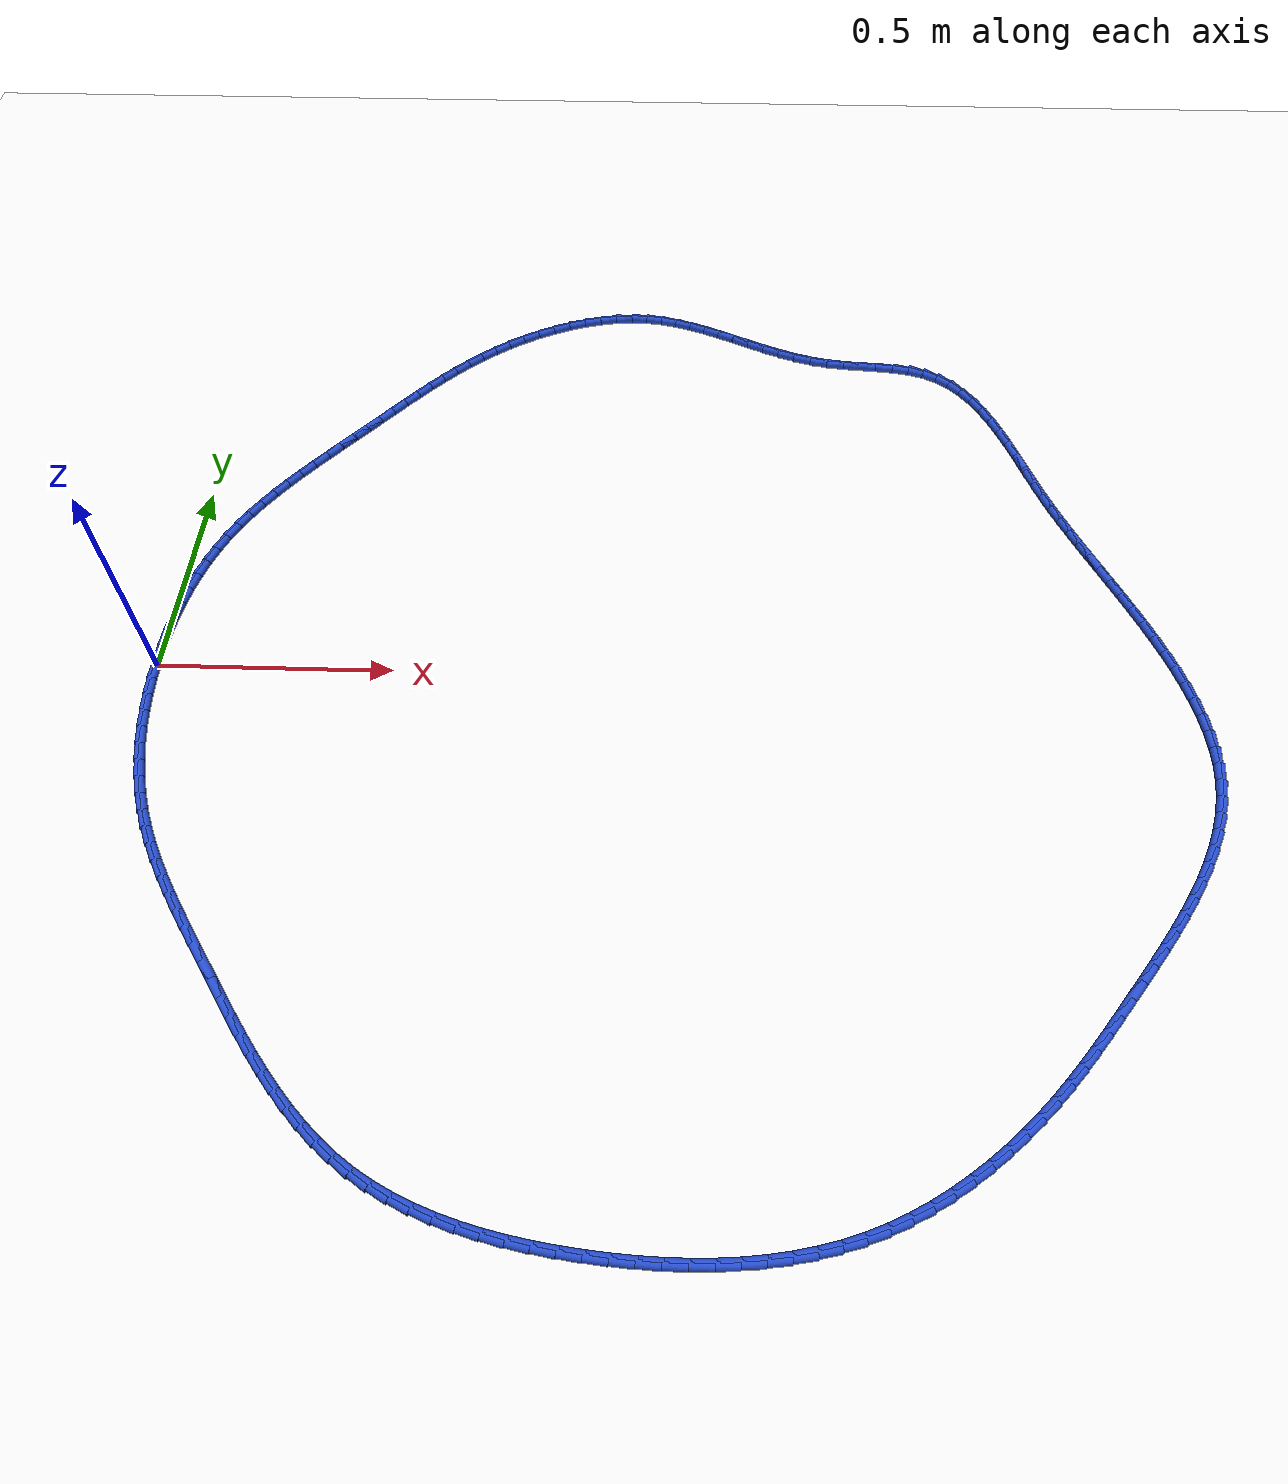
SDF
<sdf version="1.6">
 <world name="default">
  <light name="sun" type="directional">
   <pose>0 0 10 0 -0 0</pose>
   <diffuse>0.8 0.8 0.8 1</diffuse>
   <specular>0.2 0.2 0.2 1</specular>
   <attenuation>
    <range>1000</range>
    <constant>0.9</constant>
    <linear>0.01</linear>
    <quadratic>0.001</quadratic>
   </attenuation>
   <direction>-0.5 0.1 -0.9</direction>
  </light>
  <model name="ground_plane">
   <static>1</static>
   <link name="link">
    <collision name="collision">
     <geometry><plane><normal>0 0 1</normal><size>100 100</size></plane></geometry>
     <surface><friction><ode><mu>100</mu><mu2>50</mu2></ode></friction></surface>
    </collision>
    <visual name="visual">
     <cast_shadows>0</cast_shadows>
     <geometry><plane><normal>0 0 1</normal><size>100 100</size></plane></geometry>
     <material>
      <script><uri>file://media/materials/scripts/gazebo.material</uri><name>Gazebo/WhiteGlow</name></script>
     </material>
    </visual>
   </link>
  </model>
  <gravity>0 0 -9.8</gravity>
  <magnetic_field>6e-06 2.3e-05 -4.2e-05</magnetic_field>
  <atmosphere type="adiabatic"/>
  <physics name="default_physics" default="0" type="ode">
   <max_step_size>0.001</max_step_size>
   <real_time_factor>1</real_time_factor>
   <real_time_update_rate>1000</real_time_update_rate>
  </physics>
  <scene><ambient>0.4 0.4 0.4 1</ambient><background>0.7 0.7 0.7 1</background><shadows>1</shadows></scene>
  <spherical_coordinates>
   <surface_model>EARTH_WGS84</surface_model>
   <latitude_deg>0</latitude_deg>
   <longitude_deg>0</longitude_deg>
   <elevation>0</elevation>
   <heading_deg>0</heading_deg>
  </spherical_coordinates>
  <model name="line">
   <link name="link_0">
    <pose>3.469446951953614e-18 0.0 0.01 0 1.57 1.557081055174507</pose>
    <collision name="collision">
     <geometry><cylinder><radius>0.01</radius><length>0.08</length></cylinder></geometry>
    </collision>
    <visual name="visual">
     <material>
      <script><name>Gazebo/Blue</name><uri>file://media/materials/scripts/gazebo.material</uri></script>
     </material>
     <geometry><cylinder><radius>0.01</radius><length>0.08</length></cylinder></geometry>
    </visual>
   </link>
   <link name="link_1">
    <pose>0.0005698389230910422 0.041545162783905173 0.01 0 1.57 1.5200972994835111</pose>
    <collision name="collision">
     <geometry><cylinder><radius>0.01</radius><length>0.08</length></cylinder></geometry>
    </collision>
    <visual name="visual">
     <material>
      <script><name>Gazebo/Blue</name><uri>file://media/materials/scripts/gazebo.material</uri></script>
     </material>
     <geometry><cylinder><radius>0.01</radius><length>0.08</length></cylinder></geometry>
    </visual>
   </link>
   <link name="link_2">
    <pose>0.0026732887614002825 0.08299856753516024 0.01 0 1.57 1.4808727191318776</pose>
    <collision name="collision">
     <geometry><cylinder><radius>0.01</radius><length>0.08</length></cylinder></geometry>
    </collision>
    <visual name="visual">
     <material>
      <script><name>Gazebo/Blue</name><uri>file://media/materials/scripts/gazebo.material</uri></script>
     </material>
     <geometry><cylinder><radius>0.01</radius><length>0.08</length></cylinder></geometry>
    </visual>
   </link>
   <link name="link_3">
    <pose>0.006391847719253517 0.12423946716694735 0.01 0 1.57 1.4391861110435986</pose>
    <collision name="collision">
     <geometry><cylinder><radius>0.01</radius><length>0.08</length></cylinder></geometry>
    </collision>
    <visual name="visual">
     <material>
      <script><name>Gazebo/Blue</name><uri>file://media/materials/scripts/gazebo.material</uri></script>
     </material>
     <geometry><cylinder><radius>0.01</radius><length>0.08</length></cylinder></geometry>
    </visual>
   </link>
   <link name="link_4">
    <pose>0.011807014000976564 0.1651471145924485 0.01 0 1.57 1.3948204671441984</pose>
    <collision name="collision">
     <geometry><cylinder><radius>0.01</radius><length>0.08</length></cylinder></geometry>
    </collision>
    <visual name="visual">
     <material>
      <script><name>Gazebo/Blue</name><uri>file://media/materials/scripts/gazebo.material</uri></script>
     </material>
     <geometry><cylinder><radius>0.01</radius><length>0.08</length></cylinder></geometry>
    </visual>
   </link>
   <link name="link_5">
    <pose>0.019000285810895218 0.20560076272484573 0.01 0 1.57 1.3475703724889114</pose>
    <collision name="collision">
     <geometry><cylinder><radius>0.01</radius><length>0.08</length></cylinder></geometry>
    </collision>
    <visual name="visual">
     <material>
      <script><name>Gazebo/Blue</name><uri>file://media/materials/scripts/gazebo.material</uri></script>
     </material>
     <geometry><cylinder><radius>0.01</radius><length>0.08</length></cylinder></geometry>
    </visual>
   </link>
   <link name="link_6">
    <pose>0.028053161353335274 0.24547966447732103 0.01 0 1.57 1.2972523128864661</pose>
    <collision name="collision">
     <geometry><cylinder><radius>0.01</radius><length>0.08</length></cylinder></geometry>
    </collision>
    <visual name="visual">
     <material>
      <script><name>Gazebo/Blue</name><uri>file://media/materials/scripts/gazebo.material</uri></script>
     </material>
     <geometry><cylinder><radius>0.01</radius><length>0.08</length></cylinder></geometry>
    </visual>
   </link>
   <link name="link_7">
    <pose>0.03904713883262256 0.28466307276305663 0.01 0 1.57 1.2437181974995577</pose>
    <collision name="collision">
     <geometry><cylinder><radius>0.01</radius><length>0.08</length></cylinder></geometry>
    </collision>
    <visual name="visual">
     <material>
      <script><name>Gazebo/Blue</name><uri>file://media/materials/scripts/gazebo.material</uri></script>
     </material>
     <geometry><cylinder><radius>0.01</radius><length>0.08</length></cylinder></geometry>
    </visual>
   </link>
   <link name="link_8">
    <pose>0.05206371645308286 0.32303024049523443 0.01 0 1.57 1.1868720875243683</pose>
    <collision name="collision">
     <geometry><cylinder><radius>0.01</radius><length>0.08</length></cylinder></geometry>
    </collision>
    <visual name="visual">
     <material>
      <script><name>Gazebo/Blue</name><uri>file://media/materials/scripts/gazebo.material</uri></script>
     </material>
     <geometry><cylinder><radius>0.01</radius><length>0.08</length></cylinder></geometry>
    </visual>
   </link>
   <link name="link_9">
    <pose>0.067184392419042 0.36046042058703653 0.01 0 1.57 1.1281532758197523</pose>
    <collision name="collision">
     <geometry><cylinder><radius>0.01</radius><length>0.08</length></cylinder></geometry>
    </collision>
    <visual name="visual">
     <material>
      <script><name>Gazebo/Blue</name><uri>file://media/materials/scripts/gazebo.material</uri></script>
     </material>
     <geometry><cylinder><radius>0.01</radius><length>0.08</length></cylinder></geometry>
    </visual>
   </link>
   <link name="link_10">
    <pose>0.08444208644708855 0.3968680285939213 0.01 0 1.57 1.0739623734600916</pose>
    <collision name="collision">
     <geometry><cylinder><radius>0.01</radius><length>0.08</length></cylinder></geometry>
    </collision>
    <visual name="visual">
     <material>
      <script><name>Gazebo/Blue</name><uri>file://media/materials/scripts/gazebo.material</uri></script>
     </material>
     <geometry><cylinder><radius>0.01</radius><length>0.08</length></cylinder></geometry>
    </visual>
   </link>
   <link name="link_11">
    <pose>0.10366266211209786 0.43231735384019665 0.01 0 1.57 1.0262000147101982</pose>
    <collision name="collision">
     <geometry><cylinder><radius>0.01</radius><length>0.08</length></cylinder></geometry>
    </collision>
    <visual name="visual">
     <material>
      <script><name>Gazebo/Blue</name><uri>file://media/materials/scripts/gazebo.material</uri></script>
     </material>
     <geometry><cylinder><radius>0.01</radius><length>0.08</length></cylinder></geometry>
    </visual>
   </link>
   <link name="link_12">
    <pose>0.12461682725414372 0.4669126091114115 0.01 0 1.57 0.9849473850095529</pose>
    <collision name="collision">
     <geometry><cylinder><radius>0.01</radius><length>0.08</length></cylinder></geometry>
    </collision>
    <visual name="visual">
     <material>
      <script><name>Gazebo/Blue</name><uri>file://media/materials/scripts/gazebo.material</uri></script>
     </material>
     <geometry><cylinder><radius>0.01</radius><length>0.08</length></cylinder></geometry>
    </visual>
   </link>
   <link name="link_13">
    <pose>0.1470752892221213 0.5007580075486453 0.01 0 1.57 0.9501609036371669</pose>
    <collision name="collision">
     <geometry><cylinder><radius>0.01</radius><length>0.08</length></cylinder></geometry>
    </collision>
    <visual name="visual">
     <material>
      <script><name>Gazebo/Blue</name><uri>file://media/materials/scripts/gazebo.material</uri></script>
     </material>
     <geometry><cylinder><radius>0.01</radius><length>0.08</length></cylinder></geometry>
    </visual>
   </link>
   <link name="link_14">
    <pose>0.17080875536492568 0.533957762292977 0.01 0 1.57 0.9217250289088585</pose>
    <collision name="collision">
     <geometry><cylinder><radius>0.01</radius><length>0.08</length></cylinder></geometry>
    </collision>
    <visual name="visual">
     <material>
      <script><name>Gazebo/Blue</name><uri>file://media/materials/scripts/gazebo.material</uri></script>
     </material>
     <geometry><cylinder><radius>0.01</radius><length>0.08</length></cylinder></geometry>
    </visual>
   </link>
   <link name="link_15">
    <pose>0.19558793303145225 0.5666160864854863 0.01 0 1.57 0.8994955455293171</pose>
    <collision name="collision">
     <geometry><cylinder><radius>0.01</radius><length>0.08</length></cylinder></geometry>
    </collision>
    <visual name="visual">
     <material>
      <script><name>Gazebo/Blue</name><uri>file://media/materials/scripts/gazebo.material</uri></script>
     </material>
     <geometry><cylinder><radius>0.01</radius><length>0.08</length></cylinder></geometry>
    </visual>
   </link>
   <link name="link_16">
    <pose>0.22118352957059623 0.5988371932672524 0.01 0 1.57 0.8833324995591779</pose>
    <collision name="collision">
     <geometry><cylinder><radius>0.01</radius><length>0.08</length></cylinder></geometry>
    </collision>
    <visual name="visual">
     <material>
      <script><name>Gazebo/Blue</name><uri>file://media/materials/scripts/gazebo.material</uri></script>
     </material>
     <geometry><cylinder><radius>0.01</radius><length>0.08</length></cylinder></geometry>
    </visual>
   </link>
   <link name="link_17">
    <pose>0.24736625233125267 0.6307252957793547 0.01 0 1.57 0.8731237472667347</pose>
    <collision name="collision">
     <geometry><cylinder><radius>0.01</radius><length>0.08</length></cylinder></geometry>
    </collision>
    <visual name="visual">
     <material>
      <script><name>Gazebo/Blue</name><uri>file://media/materials/scripts/gazebo.material</uri></script>
     </material>
     <geometry><cylinder><radius>0.01</radius><length>0.08</length></cylinder></geometry>
    </visual>
   </link>
   <link name="link_18">
    <pose>0.2739068086623168 0.6623846071628722 0.01 0 1.57 0.8688007347777467</pose>
    <collision name="collision">
     <geometry><cylinder><radius>0.01</radius><length>0.08</length></cylinder></geometry>
    </collision>
    <visual name="visual">
     <material>
      <script><name>Gazebo/Blue</name><uri>file://media/materials/scripts/gazebo.material</uri></script>
     </material>
     <geometry><cylinder><radius>0.01</radius><length>0.08</length></cylinder></geometry>
    </visual>
   </link>
   <link name="link_19">
    <pose>0.300575905912684 0.6939193405588848 0.01 0 1.57 0.870348034622025</pose>
    <collision name="collision">
     <geometry><cylinder><radius>0.01</radius><length>0.08</length></cylinder></geometry>
    </collision>
    <visual name="visual">
     <material>
      <script><name>Gazebo/Blue</name><uri>file://media/materials/scripts/gazebo.material</uri></script>
     </material>
     <geometry><cylinder><radius>0.01</radius><length>0.08</length></cylinder></geometry>
    </visual>
   </link>
   <link name="link_20">
    <pose>0.32714425179915124 0.7254337088915553 0.01 0 1.57 0.8757457678776526</pose>
    <collision name="collision">
     <geometry><cylinder><radius>0.01</radius><length>0.08</length></cylinder></geometry>
    </collision>
    <visual name="visual">
     <material>
      <script><name>Gazebo/Blue</name><uri>file://media/materials/scripts/gazebo.material</uri></script>
     </material>
     <geometry><cylinder><radius>0.01</radius><length>0.08</length></cylinder></geometry>
    </visual>
   </link>
   <link name="link_21">
    <pose>0.35345647827845283 0.7569883390534942 0.01 0 1.57 0.8771884511652528</pose>
    <collision name="collision">
     <geometry><cylinder><radius>0.01</radius><length>0.08</length></cylinder></geometry>
    </collision>
    <visual name="visual">
     <material>
      <script><name>Gazebo/Blue</name><uri>file://media/materials/scripts/gazebo.material</uri></script>
     </material>
     <geometry><cylinder><radius>0.01</radius><length>0.08</length></cylinder></geometry>
    </visual>
   </link>
   <link name="link_22">
    <pose>0.37963790560141136 0.7884783629812221 0.01 0 1.57 0.87276877056563</pose>
    <collision name="collision">
     <geometry><cylinder><radius>0.01</radius><length>0.08</length></cylinder></geometry>
    </collision>
    <visual name="visual">
     <material>
      <script><name>Gazebo/Blue</name><uri>file://media/materials/scripts/gazebo.material</uri></script>
     </material>
     <geometry><cylinder><radius>0.01</radius><length>0.08</length></cylinder></geometry>
    </visual>
   </link>
   <link name="link_23">
    <pose>0.40588046252908605 0.8197596399635972 0.01 0 1.57 0.8624391260932672</pose>
    <collision name="collision">
     <geometry><cylinder><radius>0.01</radius><length>0.08</length></cylinder></geometry>
    </collision>
    <visual name="visual">
     <material>
      <script><name>Gazebo/Blue</name><uri>file://media/materials/scripts/gazebo.material</uri></script>
     </material>
     <geometry><cylinder><radius>0.01</radius><length>0.08</length></cylinder></geometry>
    </visual>
   </link>
   <link name="link_24">
    <pose>0.4323760778225356 0.8506880292894768 0.01 0 1.57 0.8461675748330334</pose>
    <collision name="collision">
     <geometry><cylinder><radius>0.01</radius><length>0.08</length></cylinder></geometry>
    </collision>
    <visual name="visual">
     <material>
      <script><name>Gazebo/Blue</name><uri>file://media/materials/scripts/gazebo.material</uri></script>
     </material>
     <geometry><cylinder><radius>0.01</radius><length>0.08</length></cylinder></geometry>
    </visual>
   </link>
   <link name="link_25">
    <pose>0.4593166802428191 0.8811193902477193 0.01 0 1.57 0.82394907151662</pose>
    <collision name="collision">
     <geometry><cylinder><radius>0.01</radius><length>0.08</length></cylinder></geometry>
    </collision>
    <visual name="visual">
     <material>
      <script><name>Gazebo/Blue</name><uri>file://media/materials/scripts/gazebo.material</uri></script>
     </material>
     <geometry><cylinder><radius>0.01</radius><length>0.08</length></cylinder></geometry>
    </visual>
   </link>
   <link name="link_26">
    <pose>0.48689419855099547 0.9109095821271822 0.01 0 1.57 0.795822905978151</pose>
    <collision name="collision">
     <geometry><cylinder><radius>0.01</radius><length>0.08</length></cylinder></geometry>
    </collision>
    <visual name="visual">
     <material>
      <script><name>Gazebo/Blue</name><uri>file://media/materials/scripts/gazebo.material</uri></script>
     </material>
     <geometry><cylinder><radius>0.01</radius><length>0.08</length></cylinder></geometry>
    </visual>
   </link>
   <link name="link_27">
    <pose>0.5153005615081233 0.9399144642167233 0.01 0 1.57 0.7618956323345664</pose>
    <collision name="collision">
     <geometry><cylinder><radius>0.01</radius><length>0.08</length></cylinder></geometry>
    </collision>
    <visual name="visual">
     <material>
      <script><name>Gazebo/Blue</name><uri>file://media/materials/scripts/gazebo.material</uri></script>
     </material>
     <geometry><cylinder><radius>0.01</radius><length>0.08</length></cylinder></geometry>
    </visual>
   </link>
   <link name="link_28">
    <pose>0.5447276978752621 0.9679898958052006 0.01 0 1.57 0.7223677445528075</pose>
    <collision name="collision">
     <geometry><cylinder><radius>0.01</radius><length>0.08</length></cylinder></geometry>
    </collision>
    <visual name="visual">
     <material>
      <script><name>Gazebo/Blue</name><uri>file://media/materials/scripts/gazebo.material</uri></script>
     </material>
     <geometry><cylinder><radius>0.01</radius><length>0.08</length></cylinder></geometry>
    </visual>
   </link>
   <link name="link_29">
    <pose>0.5753675364134704 0.994991736181472 0.01 0 1.57 0.6775609067274079</pose>
    <collision name="collision">
     <geometry><cylinder><radius>0.01</radius><length>0.08</length></cylinder></geometry>
    </collision>
    <visual name="visual">
     <material>
      <script><name>Gazebo/Blue</name><uri>file://media/materials/scripts/gazebo.material</uri></script>
     </material>
     <geometry><cylinder><radius>0.01</radius><length>0.08</length></cylinder></geometry>
    </visual>
   </link>
   <link name="link_30">
    <pose>0.6074120058838071 1.0207758446343944 0.01 0 1.57 0.627940937626922</pose>
    <collision name="collision">
     <geometry><cylinder><radius>0.01</radius><length>0.08</length></cylinder></geometry>
    </collision>
    <visual name="visual">
     <material>
      <script><name>Gazebo/Blue</name><uri>file://media/materials/scripts/gazebo.material</uri></script>
     </material>
     <geometry><cylinder><radius>0.01</radius><length>0.08</length></cylinder></geometry>
    </visual>
   </link>
   <link name="link_31">
    <pose>0.6410530350473314 1.0451980804528267 0.01 0 1.57 0.5745217246978148</pose>
    <collision name="collision">
     <geometry><cylinder><radius>0.01</radius><length>0.08</length></cylinder></geometry>
    </collision>
    <visual name="visual">
     <material>
      <script><name>Gazebo/Blue</name><uri>file://media/materials/scripts/gazebo.material</uri></script>
     </material>
     <geometry><cylinder><radius>0.01</radius><length>0.08</length></cylinder></geometry>
    </visual>
   </link>
   <link name="link_32">
    <pose>0.6764116504908415 1.0680880661145835 0.01 0 1.57 0.5190564999546649</pose>
    <collision name="collision">
     <geometry><cylinder><radius>0.01</radius><length>0.08</length></cylinder></geometry>
    </collision>
    <visual name="visual">
     <material>
      <script><name>Gazebo/Blue</name><uri>file://media/materials/scripts/gazebo.material</uri></script>
     </material>
     <geometry><cylinder><radius>0.01</radius><length>0.08</length></cylinder></geometry>
    </visual>
   </link>
   <link name="link_33">
    <pose>0.7132919896818282 1.0891581616858304 0.01 0 1.57 0.46093582858358545</pose>
    <collision name="collision">
     <geometry><cylinder><radius>0.01</radius><length>0.08</length></cylinder></geometry>
    </collision>
    <visual name="visual">
     <material>
      <script><name>Gazebo/Blue</name><uri>file://media/materials/scripts/gazebo.material</uri></script>
     </material>
     <geometry><cylinder><radius>0.01</radius><length>0.08</length></cylinder></geometry>
    </visual>
   </link>
   <link name="link_34">
    <pose>0.7514096939868172 1.1080879799227483 0.01 0 1.57 0.39892084222685315</pose>
    <collision name="collision">
     <geometry><cylinder><radius>0.01</radius><length>0.08</length></cylinder></geometry>
    </collision>
    <visual name="visual">
     <material>
      <script><name>Gazebo/Blue</name><uri>file://media/materials/scripts/gazebo.material</uri></script>
     </material>
     <geometry><cylinder><radius>0.01</radius><length>0.08</length></cylinder></geometry>
    </visual>
   </link>
   <link name="link_35">
    <pose>0.7904804007656524 1.1245571320988768 0.01 0 1.57 0.33171925631393967</pose>
    <collision name="collision">
     <geometry><cylinder><radius>0.01</radius><length>0.08</length></cylinder></geometry>
    </collision>
    <visual name="visual">
     <material>
      <script><name>Gazebo/Blue</name><uri>file://media/materials/scripts/gazebo.material</uri></script>
     </material>
     <geometry><cylinder><radius>0.01</radius><length>0.08</length></cylinder></geometry>
    </visual>
   </link>
   <link name="link_36">
    <pose>0.8302197473781776 1.1382452294877552 0.01 0 1.57 0.2579717170674096</pose>
    <collision name="collision">
     <geometry><cylinder><radius>0.01</radius><length>0.08</length></cylinder></geometry>
    </collision>
    <visual name="visual">
     <material>
      <script><name>Gazebo/Blue</name><uri>file://media/materials/scripts/gazebo.material</uri></script>
     </material>
     <geometry><cylinder><radius>0.01</radius><length>0.08</length></cylinder></geometry>
    </visual>
   </link>
   <link name="link_37">
    <pose>0.870343371184237 1.1488318833629232 0.01 0 1.57 0.1762762829172391</pose>
    <collision name="collision">
     <geometry><cylinder><radius>0.01</radius><length>0.08</length></cylinder></geometry>
    </collision>
    <visual name="visual">
     <material>
      <script><name>Gazebo/Blue</name><uri>file://media/materials/scripts/gazebo.material</uri></script>
     </material>
     <geometry><cylinder><radius>0.01</radius><length>0.08</length></cylinder></geometry>
    </visual>
   </link>
   <link name="link_38">
    <pose>0.9105669095436737 1.1559967049979187 0.01 0 1.57 0.08527418068000801</pose>
    <collision name="collision">
     <geometry><cylinder><radius>0.01</radius><length>0.08</length></cylinder></geometry>
    </collision>
    <visual name="visual">
     <material>
      <script><name>Gazebo/Blue</name><uri>file://media/materials/scripts/gazebo.material</uri></script>
     </material>
     <geometry><cylinder><radius>0.01</radius><length>0.08</length></cylinder></geometry>
    </visual>
   </link>
   <link name="link_39">
    <pose>0.9506059998163322 1.1594193056662825 0.01 0 1.57 -0.016172572762518062</pose>
    <collision name="collision">
     <geometry><cylinder><radius>0.01</radius><length>0.08</length></cylinder></geometry>
    </collision>
    <visual name="visual">
     <material>
      <script><name>Gazebo/Blue</name><uri>file://media/materials/scripts/gazebo.material</uri></script>
     </material>
     <geometry><cylinder><radius>0.01</radius><length>0.08</length></cylinder></geometry>
    </visual>
   </link>
   <link name="link_40">
    <pose>0.9901762793620563 1.1587792966415529 0.01 0 1.57 -0.1256354903825792</pose>
    <collision name="collision">
     <geometry><cylinder><radius>0.01</radius><length>0.08</length></cylinder></geometry>
    </collision>
    <visual name="visual">
     <material>
      <script><name>Gazebo/Blue</name><uri>file://media/materials/scripts/gazebo.material</uri></script>
     </material>
     <geometry><cylinder><radius>0.01</radius><length>0.08</length></cylinder></geometry>
    </visual>
   </link>
   <link name="link_41">
    <pose>1.0290447640574936 1.1538701793311599 0.01 0 1.57 -0.22454292599738765</pose>
    <collision name="collision">
     <geometry><cylinder><radius>0.01</radius><length>0.08</length></cylinder></geometry>
    </collision>
    <visual name="visual">
     <material>
      <script><name>Gazebo/Blue</name><uri>file://media/materials/scripts/gazebo.material</uri></script>
     </material>
     <geometry><cylinder><radius>0.01</radius><length>0.08</length></cylinder></geometry>
    </visual>
   </link>
   <link name="link_42">
    <pose>1.0672732975342132 1.1451389962443619 0.01 0 1.57 -0.304692625692873</pose>
    <collision name="collision">
     <geometry><cylinder><radius>0.01</radius><length>0.08</length></cylinder></geometry>
    </collision>
    <visual name="visual">
     <material>
      <script><name>Gazebo/Blue</name><uri>file://media/materials/scripts/gazebo.material</uri></script>
     </material>
     <geometry><cylinder><radius>0.01</radius><length>0.08</length></cylinder></geometry>
    </visual>
   </link>
   <link name="link_43">
    <pose>1.1050286930685729 1.1332654748265154 0.01 0 1.57 -0.3655983201610638</pose>
    <collision name="collision">
     <geometry><cylinder><radius>0.01</radius><length>0.08</length></cylinder></geometry>
    </collision>
    <visual name="visual">
     <material>
      <script><name>Gazebo/Blue</name><uri>file://media/materials/scripts/gazebo.material</uri></script>
     </material>
     <geometry><cylinder><radius>0.01</radius><length>0.08</length></cylinder></geometry>
    </visual>
   </link>
   <link name="link_44">
    <pose>1.1424778916945804 1.1189296257218084 0.01 0 1.57 -0.4077908570501717</pose>
    <collision name="collision">
     <geometry><cylinder><radius>0.01</radius><length>0.08</length></cylinder></geometry>
    </collision>
    <visual name="visual">
     <material>
      <script><name>Gazebo/Blue</name><uri>file://media/materials/scripts/gazebo.material</uri></script>
     </material>
     <geometry><cylinder><radius>0.01</radius><length>0.08</length></cylinder></geometry>
    </visual>
   </link>
   <link name="link_45">
    <pose>1.1797878344462438 1.1028114595744296 0.01 0 1.57 -0.4321366338775718</pose>
    <collision name="collision">
     <geometry><cylinder><radius>0.01</radius><length>0.08</length></cylinder></geometry>
    </collision>
    <visual name="visual">
     <material>
      <script><name>Gazebo/Blue</name><uri>file://media/materials/scripts/gazebo.material</uri></script>
     </material>
     <geometry><cylinder><radius>0.01</radius><length>0.08</length></cylinder></geometry>
    </visual>
   </link>
   <link name="link_46">
    <pose>1.2171254623575711 1.0855909870285672 0.01 0 1.57 -0.4394178192543434</pose>
    <collision name="collision">
     <geometry><cylinder><radius>0.01</radius><length>0.08</length></cylinder></geometry>
    </collision>
    <visual name="visual">
     <material>
      <script><name>Gazebo/Blue</name><uri>file://media/materials/scripts/gazebo.material</uri></script>
     </material>
     <geometry><cylinder><radius>0.01</radius><length>0.08</length></cylinder></geometry>
    </visual>
   </link>
   <link name="link_47">
    <pose>1.2546577164625718 1.0679482187284095 0.01 0 1.57 -0.43013408966286065</pose>
    <collision name="collision">
     <geometry><cylinder><radius>0.01</radius><length>0.08</length></cylinder></geometry>
    </collision>
    <visual name="visual">
     <material>
      <script><name>Gazebo/Blue</name><uri>file://media/materials/scripts/gazebo.material</uri></script>
     </material>
     <geometry><cylinder><radius>0.01</radius><length>0.08</length></cylinder></geometry>
    </visual>
   </link>
   <link name="link_48">
    <pose>1.2925515377952521 1.050563165318145 0.01 0 1.57 -0.40446547660785526</pose>
    <collision name="collision">
     <geometry><cylinder><radius>0.01</radius><length>0.08</length></cylinder></geometry>
    </collision>
    <visual name="visual">
     <material>
      <script><name>Gazebo/Blue</name><uri>file://media/materials/scripts/gazebo.material</uri></script>
     </material>
     <geometry><cylinder><radius>0.01</radius><length>0.08</length></cylinder></geometry>
    </visual>
   </link>
   <link name="link_49">
    <pose>1.330973867389621 1.0341158374419626 0.01 0 1.57 -0.362361269226547</pose>
    <collision name="collision">
     <geometry><cylinder><radius>0.01</radius><length>0.08</length></cylinder></geometry>
    </collision>
    <visual name="visual">
     <material>
      <script><name>Gazebo/Blue</name><uri>file://media/materials/scripts/gazebo.material</uri></script>
     </material>
     <geometry><cylinder><radius>0.01</radius><length>0.08</length></cylinder></geometry>
    </visual>
   </link>
   <link name="link_50">
    <pose>1.370091646279687 1.0192862457440495 0.01 0 1.57 -0.30375150003740936</pose>
    <collision name="collision">
     <geometry><cylinder><radius>0.01</radius><length>0.08</length></cylinder></geometry>
    </collision>
    <visual name="visual">
     <material>
      <script><name>Gazebo/Blue</name><uri>file://media/materials/scripts/gazebo.material</uri></script>
     </material>
     <geometry><cylinder><radius>0.01</radius><length>0.08</length></cylinder></geometry>
    </visual>
   </link>
   <link name="link_51">
    <pose>1.410071815499458 1.006754400868595 0.01 0 1.57 -0.22888973912910016</pose>
    <collision name="collision">
     <geometry><cylinder><radius>0.01</radius><length>0.08</length></cylinder></geometry>
    </collision>
    <visual name="visual">
     <material>
      <script><name>Gazebo/Blue</name><uri>file://media/materials/scripts/gazebo.material</uri></script>
     </material>
     <geometry><cylinder><radius>0.01</radius><length>0.08</length></cylinder></geometry>
    </visual>
   </link>
   <link name="link_52">
    <pose>1.4510813160829426 0.9972003134597871 0.01 0 1.57 -0.14556922707870218</pose>
    <collision name="collision">
     <geometry><cylinder><radius>0.01</radius><length>0.08</length></cylinder></geometry>
    </collision>
    <visual name="visual">
     <material>
      <script><name>Gazebo/Blue</name><uri>file://media/materials/scripts/gazebo.material</uri></script>
     </material>
     <geometry><cylinder><radius>0.01</radius><length>0.08</length></cylinder></geometry>
    </visual>
   </link>
   <link name="link_53">
    <pose>1.4931699707252928 0.9910298540037658 0.01 0 1.57 -0.09105831924694072</pose>
    <collision name="collision">
     <geometry><cylinder><radius>0.01</radius><length>0.08</length></cylinder></geometry>
    </collision>
    <visual name="visual">
     <material>
      <script><name>Gazebo/Blue</name><uri>file://media/materials/scripts/gazebo.material</uri></script>
     </material>
     <geometry><cylinder><radius>0.01</radius><length>0.08</length></cylinder></geometry>
    </visual>
   </link>
   <link name="link_54">
    <pose>1.535743990738294 0.9871423848848361 0.01 0 1.57 -0.07607122398688305</pose>
    <collision name="collision">
     <geometry><cylinder><radius>0.01</radius><length>0.08</length></cylinder></geometry>
    </collision>
    <visual name="visual">
     <material>
      <script><name>Gazebo/Blue</name><uri>file://media/materials/scripts/gazebo.material</uri></script>
     </material>
     <geometry><cylinder><radius>0.01</radius><length>0.08</length></cylinder></geometry>
    </visual>
   </link>
   <link name="link_55">
    <pose>1.5779896640353046 0.9839224914182927 0.01 0 1.57 -0.10106160086372763</pose>
    <collision name="collision">
     <geometry><cylinder><radius>0.01</radius><length>0.08</length></cylinder></geometry>
    </collision>
    <visual name="visual">
     <material>
      <script><name>Gazebo/Blue</name><uri>file://media/materials/scripts/gazebo.material</uri></script>
     </material>
     <geometry><cylinder><radius>0.01</radius><length>0.08</length></cylinder></geometry>
    </visual>
   </link>
   <link name="link_56">
    <pose>1.6190930881992849 0.9797543134110152 0.01 0 1.57 -0.1703083232349127</pose>
    <collision name="collision">
     <geometry><cylinder><radius>0.01</radius><length>0.08</length></cylinder></geometry>
    </collision>
    <visual name="visual">
     <material>
      <script><name>Gazebo/Blue</name><uri>file://media/materials/scripts/gazebo.material</uri></script>
     </material>
     <geometry><cylinder><radius>0.01</radius><length>0.08</length></cylinder></geometry>
    </visual>
   </link>
   <link name="link_57">
    <pose>1.6582403608131935 0.9730219906698818 0.01 0 1.57 -0.29143566190404235</pose>
    <collision name="collision">
     <geometry><cylinder><radius>0.01</radius><length>0.08</length></cylinder></geometry>
    </collision>
    <visual name="visual">
     <material>
      <script><name>Gazebo/Blue</name><uri>file://media/materials/scripts/gazebo.material</uri></script>
     </material>
     <geometry><cylinder><radius>0.01</radius><length>0.08</length></cylinder></geometry>
    </visual>
   </link>
   <link name="link_58">
    <pose>1.6946175794599911 0.9621096630017723 0.01 0 1.57 -0.467204908797201</pose>
    <collision name="collision">
     <geometry><cylinder><radius>0.01</radius><length>0.08</length></cylinder></geometry>
    </collision>
    <visual name="visual">
     <material>
      <script><name>Gazebo/Blue</name><uri>file://media/materials/scripts/gazebo.material</uri></script>
     </material>
     <geometry><cylinder><radius>0.01</radius><length>0.08</length></cylinder></geometry>
    </visual>
   </link>
   <link name="link_59">
    <pose>1.7274779039952877 0.9455331222283423 0.01 0 1.57 -0.651654203072232</pose>
    <collision name="collision">
     <geometry><cylinder><radius>0.01</radius><length>0.08</length></cylinder></geometry>
    </collision>
    <visual name="visual">
     <material>
      <script><name>Gazebo/Blue</name><uri>file://media/materials/scripts/gazebo.material</uri></script>
     </material>
     <geometry><cylinder><radius>0.01</radius><length>0.08</length></cylinder></geometry>
    </visual>
   </link>
   <link name="link_60">
    <pose>1.7567755243015204 0.9231843738276477 0.01 0 1.57 -0.8097327409211476</pose>
    <collision name="collision">
     <geometry><cylinder><radius>0.01</radius><length>0.08</length></cylinder></geometry>
    </collision>
    <visual name="visual">
     <material>
      <script><name>Gazebo/Blue</name><uri>file://media/materials/scripts/gazebo.material</uri></script>
     </material>
     <geometry><cylinder><radius>0.01</radius><length>0.08</length></cylinder></geometry>
    </visual>
   </link>
   <link name="link_61">
    <pose>1.7828821956866072 0.895775158836842 0.01 0 1.57 -0.9378043812204923</pose>
    <collision name="collision">
     <geometry><cylinder><radius>0.01</radius><length>0.08</length></cylinder></geometry>
    </collision>
    <visual name="visual">
     <material>
      <script><name>Gazebo/Blue</name><uri>file://media/materials/scripts/gazebo.material</uri></script>
     </material>
     <geometry><cylinder><radius>0.01</radius><length>0.08</length></cylinder></geometry>
    </visual>
   </link>
   <link name="link_62">
    <pose>1.806175227324677 0.8640281212590505 0.01 0 1.57 -1.0379092024082466</pose>
    <collision name="collision">
     <geometry><cylinder><radius>0.01</radius><length>0.08</length></cylinder></geometry>
    </collision>
    <visual name="visual">
     <material>
      <script><name>Gazebo/Blue</name><uri>file://media/materials/scripts/gazebo.material</uri></script>
     </material>
     <geometry><cylinder><radius>0.01</radius><length>0.08</length></cylinder></geometry>
    </visual>
   </link>
   <link name="link_63">
    <pose>1.8270319283898602 0.8286659050973975 0.01 0 1.57 -1.1140671984465251</pose>
    <collision name="collision">
     <geometry><cylinder><radius>0.01</radius><length>0.08</length></cylinder></geometry>
    </collision>
    <visual name="visual">
     <material>
      <script><name>Gazebo/Blue</name><uri>file://media/materials/scripts/gazebo.material</uri></script>
     </material>
     <geometry><cylinder><radius>0.01</radius><length>0.08</length></cylinder></geometry>
    </visual>
   </link>
   <link name="link_64">
    <pose>1.8458296080562855 0.7904111543550083 0.01 0 1.57 -1.1702780175155891</pose>
    <collision name="collision">
     <geometry><cylinder><radius>0.01</radius><length>0.08</length></cylinder></geometry>
    </collision>
    <visual name="visual">
     <material>
      <script><name>Gazebo/Blue</name><uri>file://media/materials/scripts/gazebo.material</uri></script>
     </material>
     <geometry><cylinder><radius>0.01</radius><length>0.08</length></cylinder></geometry>
    </visual>
   </link>
   <link name="link_65">
    <pose>1.8629455754980824 0.7499865130350073 0.01 0 1.57 -1.2097326977177658</pose>
    <collision name="collision">
     <geometry><cylinder><radius>0.01</radius><length>0.08</length></cylinder></geometry>
    </collision>
    <visual name="visual">
     <material>
      <script><name>Gazebo/Blue</name><uri>file://media/materials/scripts/gazebo.material</uri></script>
     </material>
     <geometry><cylinder><radius>0.01</radius><length>0.08</length></cylinder></geometry>
    </visual>
   </link>
   <link name="link_66">
    <pose>1.8787571398893825 0.7081146251405196 0.01 0 1.57 -1.2346298351911302</pose>
    <collision name="collision">
     <geometry><cylinder><radius>0.01</radius><length>0.08</length></cylinder></geometry>
    </collision>
    <visual name="visual">
     <material>
      <script><name>Gazebo/Blue</name><uri>file://media/materials/scripts/gazebo.material</uri></script>
     </material>
     <geometry><cylinder><radius>0.01</radius><length>0.08</length></cylinder></geometry>
    </visual>
   </link>
   <link name="link_67">
    <pose>1.8936416104043123 0.6655181346746698 0.01 0 1.57 -1.2461919962147716</pose>
    <collision name="collision">
     <geometry><cylinder><radius>0.01</radius><length>0.08</length></cylinder></geometry>
    </collision>
    <visual name="visual">
     <material>
      <script><name>Gazebo/Blue</name><uri>file://media/materials/scripts/gazebo.material</uri></script>
     </material>
     <geometry><cylinder><radius>0.01</radius><length>0.08</length></cylinder></geometry>
    </visual>
   </link>
   <link name="link_68">
    <pose>1.907976296217004 0.6229196856405828 0.01 0 1.57 -1.2446903861384637</pose>
    <collision name="collision">
     <geometry><cylinder><radius>0.01</radius><length>0.08</length></cylinder></geometry>
    </collision>
    <visual name="visual">
     <material>
      <script><name>Gazebo/Blue</name><uri>file://media/materials/scripts/gazebo.material</uri></script>
     </material>
     <geometry><cylinder><radius>0.01</radius><length>0.08</length></cylinder></geometry>
    </visual>
   </link>
   <link name="link_69">
    <pose>1.9221385065015855 0.5810419220413836 0.01 0 1.57 -1.2297043760029835</pose>
    <collision name="collision">
     <geometry><cylinder><radius>0.01</radius><length>0.08</length></cylinder></geometry>
    </collision>
    <visual name="visual">
     <material>
      <script><name>Gazebo/Blue</name><uri>file://media/materials/scripts/gazebo.material</uri></script>
     </material>
     <geometry><cylinder><radius>0.01</radius><length>0.08</length></cylinder></geometry>
    </visual>
   </link>
   <link name="link_70">
    <pose>1.9364989678412887 0.5405860367387119 0.01 0 1.57 -1.2078678131129432</pose>
    <collision name="collision">
     <geometry><cylinder><radius>0.01</radius><length>0.08</length></cylinder></geometry>
    </collision>
    <visual name="visual">
     <material>
      <script><name>Gazebo/Blue</name><uri>file://media/materials/scripts/gazebo.material</uri></script>
     </material>
     <geometry><cylinder><radius>0.01</radius><length>0.08</length></cylinder></geometry>
    </visual>
   </link>
   <link name="link_71">
    <pose>1.9512619036106462 0.5017106271416624 0.01 0 1.57 -1.1877509499258085</pose>
    <collision name="collision">
     <geometry><cylinder><radius>0.01</radius><length>0.08</length></cylinder></geometry>
    </collision>
    <visual name="visual">
     <material>
      <script><name>Gazebo/Blue</name><uri>file://media/materials/scripts/gazebo.material</uri></script>
     </material>
     <geometry><cylinder><radius>0.01</radius><length>0.08</length></cylinder></geometry>
    </visual>
   </link>
   <link name="link_72">
    <pose>1.9664561839854646 0.46400285513588974 0.01 0 1.57 -1.170540226670106</pose>
    <collision name="collision">
     <geometry><cylinder><radius>0.01</radius><length>0.08</length></cylinder></geometry>
    </collision>
    <visual name="visual">
     <material>
      <script><name>Gazebo/Blue</name><uri>file://media/materials/scripts/gazebo.material</uri></script>
     </material>
     <geometry><cylinder><radius>0.01</radius><length>0.08</length></cylinder></geometry>
    </visual>
   </link>
   <link name="link_73">
    <pose>1.9821023250644019 0.4270226586015313 0.01 0 1.57 -1.156889265317586</pose>
    <collision name="collision">
     <geometry><cylinder><radius>0.01</radius><length>0.08</length></cylinder></geometry>
    </collision>
    <visual name="visual">
     <material>
      <script><name>Gazebo/Blue</name><uri>file://media/materials/scripts/gazebo.material</uri></script>
     </material>
     <geometry><cylinder><radius>0.01</radius><length>0.08</length></cylinder></geometry>
    </visual>
   </link>
   <link name="link_74">
    <pose>1.9982208429461146 0.3903299754187243 0.01 0 1.57 -1.1472416754130788</pose>
    <collision name="collision">
     <geometry><cylinder><radius>0.01</radius><length>0.08</length></cylinder></geometry>
    </collision>
    <visual name="visual">
     <material>
      <script><name>Gazebo/Blue</name><uri>file://media/materials/scripts/gazebo.material</uri></script>
     </material>
     <geometry><cylinder><radius>0.01</radius><length>0.08</length></cylinder></geometry>
    </visual>
   </link>
   <link name="link_75">
    <pose>2.014832253729259 0.35348474346760705 0.01 0 1.57 -1.1418934570154329</pose>
    <collision name="collision">
     <geometry><cylinder><radius>0.01</radius><length>0.08</length></cylinder></geometry>
    </collision>
    <visual name="visual">
     <material>
      <script><name>Gazebo/Blue</name><uri>file://media/materials/scripts/gazebo.material</uri></script>
     </material>
     <geometry><cylinder><radius>0.01</radius><length>0.08</length></cylinder></geometry>
    </visual>
   </link>
   <link name="link_76">
    <pose>2.031931460052398 0.31609257586505746 0.01 0 1.57 -1.1414966649964253</pose>
    <collision name="collision">
     <geometry><cylinder><radius>0.01</radius><length>0.08</length></cylinder></geometry>
    </collision>
    <visual name="visual">
     <material>
      <script><name>Gazebo/Blue</name><uri>file://media/materials/scripts/gazebo.material</uri></script>
     </material>
     <geometry><cylinder><radius>0.01</radius><length>0.08</length></cylinder></geometry>
    </visual>
   </link>
   <link name="link_77">
    <pose>2.0493291109516774 0.27808765620924647 0.01 0 1.57 -1.1461476384611202</pose>
    <collision name="collision">
     <geometry><cylinder><radius>0.01</radius><length>0.08</length></cylinder></geometry>
    </collision>
    <visual name="visual">
     <material>
      <script><name>Gazebo/Blue</name><uri>file://media/materials/scripts/gazebo.material</uri></script>
     </material>
     <geometry><cylinder><radius>0.01</radius><length>0.08</length></cylinder></geometry>
    </visual>
   </link>
   <link name="link_78">
    <pose>2.0667552064084393 0.23954798563246404 0.01 0 1.57 -1.1557301008856284</pose>
    <collision name="collision">
     <geometry><cylinder><radius>0.01</radius><length>0.08</length></cylinder></geometry>
    </collision>
    <visual name="visual">
     <material>
      <script><name>Gazebo/Blue</name><uri>file://media/materials/scripts/gazebo.material</uri></script>
     </material>
     <geometry><cylinder><radius>0.01</radius><length>0.08</length></cylinder></geometry>
    </visual>
   </link>
   <link name="link_79">
    <pose>2.083939405638078 0.2005521729383297 0.01 0 1.57 -1.1702539449690073</pose>
    <collision name="collision">
     <geometry><cylinder><radius>0.01</radius><length>0.08</length></cylinder></geometry>
    </collision>
    <visual name="visual">
     <material>
      <script><name>Gazebo/Blue</name><uri>file://media/materials/scripts/gazebo.material</uri></script>
     </material>
     <geometry><cylinder><radius>0.01</radius><length>0.08</length></cylinder></geometry>
    </visual>
   </link>
   <link name="link_80">
    <pose>2.1006113678559863 0.1611788269304645 0.01 0 1.57 -1.189845085638293</pose>
    <collision name="collision">
     <geometry><cylinder><radius>0.01</radius><length>0.08</length></cylinder></geometry>
    </collision>
    <visual name="visual">
     <material>
      <script><name>Gazebo/Blue</name><uri>file://media/materials/scripts/gazebo.material</uri></script>
     </material>
     <geometry><cylinder><radius>0.01</radius><length>0.08</length></cylinder></geometry>
    </visual>
   </link>
   <link name="link_81">
    <pose>2.11650075227756 0.12150655641248828 0.01 0 1.57 -1.214737135405417</pose>
    <collision name="collision">
     <geometry><cylinder><radius>0.01</radius><length>0.08</length></cylinder></geometry>
    </collision>
    <visual name="visual">
     <material>
      <script><name>Gazebo/Blue</name><uri>file://media/materials/scripts/gazebo.material</uri></script>
     </material>
     <geometry><cylinder><radius>0.01</radius><length>0.08</length></cylinder></geometry>
    </visual>
   </link>
   <link name="link_82">
    <pose>2.131337218118192 0.08161397018802098 0.01 0 1.57 -1.2452638633154385</pose>
    <collision name="collision">
     <geometry><cylinder><radius>0.01</radius><length>0.08</length></cylinder></geometry>
    </collision>
    <visual name="visual">
     <material>
      <script><name>Gazebo/Blue</name><uri>file://media/materials/scripts/gazebo.material</uri></script>
     </material>
     <geometry><cylinder><radius>0.01</radius><length>0.08</length></cylinder></geometry>
    </visual>
   </link>
   <link name="link_83">
    <pose>2.1448504245932765 0.041579677060683586 0.01 0 1.57 -1.2818493238910404</pose>
    <collision name="collision">
     <geometry><cylinder><radius>0.01</radius><length>0.08</length></cylinder></geometry>
    </collision>
    <visual name="visual">
     <material>
      <script><name>Gazebo/Blue</name><uri>file://media/materials/scripts/gazebo.material</uri></script>
     </material>
     <geometry><cylinder><radius>0.01</radius><length>0.08</length></cylinder></geometry>
    </visual>
   </link>
   <link name="link_84">
    <pose>2.156770030918208 0.001482285834095709 0.01 0 1.57 -1.324991402529761</pose>
    <collision name="collision">
     <geometry><cylinder><radius>0.01</radius><length>0.08</length></cylinder></geometry>
    </collision>
    <visual name="visual">
     <material>
      <script><name>Gazebo/Blue</name><uri>file://media/materials/scripts/gazebo.material</uri></script>
     </material>
     <geometry><cylinder><radius>0.01</radius><length>0.08</length></cylinder></geometry>
    </visual>
   </link>
   <link name="link_85">
    <pose>2.1668256963083787 -0.03859959468812169 0.01 0 1.57 -1.375232970775576</pose>
    <collision name="collision">
     <geometry><cylinder><radius>0.01</radius><length>0.08</length></cylinder></geometry>
    </collision>
    <visual name="visual">
     <material>
      <script><name>Gazebo/Blue</name><uri>file://media/materials/scripts/gazebo.material</uri></script>
     </material>
     <geometry><cylinder><radius>0.01</radius><length>0.08</length></cylinder></geometry>
    </visual>
   </link>
   <link name="link_86">
    <pose>2.1747470799791855 -0.07858735570234868 0.01 0 1.57 -1.433113222860227</pose>
    <collision name="collision">
     <geometry><cylinder><radius>0.01</radius><length>0.08</length></cylinder></geometry>
    </collision>
    <visual name="visual">
     <material>
      <script><name>Gazebo/Blue</name><uri>file://media/materials/scripts/gazebo.material</uri></script>
     </material>
     <geometry><cylinder><radius>0.01</radius><length>0.08</length></cylinder></geometry>
    </visual>
   </link>
   <link name="link_87">
    <pose>2.1802638411460196 -0.11840238840496489 0.01 0 1.57 -1.4990910510602626</pose>
    <collision name="collision">
     <geometry><cylinder><radius>0.01</radius><length>0.08</length></cylinder></geometry>
    </collision>
    <visual name="visual">
     <material>
      <script><name>Gazebo/Blue</name><uri>file://media/materials/scripts/gazebo.material</uri></script>
     </material>
     <geometry><cylinder><radius>0.01</radius><length>0.08</length></cylinder></geometry>
    </visual>
   </link>
   <link name="link_88">
    <pose>2.1831056390242765 -0.15796608399235024 0.01 0 1.57 1.5681581401401632</pose>
    <collision name="collision">
     <geometry><cylinder><radius>0.01</radius><length>0.08</length></cylinder></geometry>
    </collision>
    <visual name="visual">
     <material>
      <script><name>Gazebo/Blue</name><uri>file://media/materials/scripts/gazebo.material</uri></script>
     </material>
     <geometry><cylinder><radius>0.01</radius><length>0.08</length></cylinder></geometry>
    </visual>
   </link>
   <link name="link_89">
    <pose>2.1830021328293503 -0.197199833660885 0.01 0 1.57 1.485514067327752</pose>
    <collision name="collision">
     <geometry><cylinder><radius>0.01</radius><length>0.08</length></cylinder></geometry>
    </collision>
    <visual name="visual">
     <material>
      <script><name>Gazebo/Blue</name><uri>file://media/materials/scripts/gazebo.material</uri></script>
     </material>
     <geometry><cylinder><radius>0.01</radius><length>0.08</length></cylinder></geometry>
    </visual>
   </link>
   <link name="link_90">
    <pose>2.179682981776634 -0.23602502860694746 0.01 0 1.57 1.3962677368109608</pose>
    <collision name="collision">
     <geometry><cylinder><radius>0.01</radius><length>0.08</length></cylinder></geometry>
    </collision>
    <visual name="visual">
     <material>
      <script><name>Gazebo/Blue</name><uri>file://media/materials/scripts/gazebo.material</uri></script>
     </material>
     <geometry><cylinder><radius>0.01</radius><length>0.08</length></cylinder></geometry>
    </visual>
   </link>
   <link name="link_91">
    <pose>2.1729219801116586 -0.27436954648941725 0.01 0 1.57 1.3107190084362488</pose>
    <collision name="collision">
     <geometry><cylinder><radius>0.01</radius><length>0.08</length></cylinder></geometry>
    </collision>
    <visual name="visual">
     <material>
      <script><name>Gazebo/Blue</name><uri>file://media/materials/scripts/gazebo.material</uri></script>
     </material>
     <geometry><cylinder><radius>0.01</radius><length>0.08</length></cylinder></geometry>
    </visual>
   </link>
   <link name="link_92">
    <pose>2.1628514195876662 -0.3122139528351244 0.01 0 1.57 1.234099878756024</pose>
    <collision name="collision">
     <geometry><cylinder><radius>0.01</radius><length>0.08</length></cylinder></geometry>
    </collision>
    <visual name="visual">
     <material>
      <script><name>Gazebo/Blue</name><uri>file://media/materials/scripts/gazebo.material</uri></script>
     </material>
     <geometry><cylinder><radius>0.01</radius><length>0.08</length></cylinder></geometry>
    </visual>
   </link>
   <link name="link_93">
    <pose>2.1497778481005487 -0.34956442334791776 0.01 0 1.57 1.1665808563955318</pose>
    <collision name="collision">
     <geometry><cylinder><radius>0.01</radius><length>0.08</length></cylinder></geometry>
    </collision>
    <visual name="visual">
     <material>
      <script><name>Gazebo/Blue</name><uri>file://media/materials/scripts/gazebo.material</uri></script>
     </material>
     <geometry><cylinder><radius>0.01</radius><length>0.08</length></cylinder></geometry>
    </visual>
   </link>
   <link name="link_94">
    <pose>2.1340089722286724 -0.3864273040215603 0.01 0 1.57 1.1079042132795962</pose>
    <collision name="collision">
     <geometry><cylinder><radius>0.01</radius><length>0.08</length></cylinder></geometry>
    </collision>
    <visual name="visual">
     <material>
      <script><name>Gazebo/Blue</name><uri>file://media/materials/scripts/gazebo.material</uri></script>
     </material>
     <geometry><cylinder><radius>0.01</radius><length>0.08</length></cylinder></geometry>
    </visual>
   </link>
   <link name="link_95">
    <pose>2.115852498550408 -0.42280894084981263 0.01 0 1.57 1.0575858795050967</pose>
    <collision name="collision">
     <geometry><cylinder><radius>0.01</radius><length>0.08</length></cylinder></geometry>
    </collision>
    <visual name="visual">
     <material>
      <script><name>Gazebo/Blue</name><uri>file://media/materials/scripts/gazebo.material</uri></script>
     </material>
     <geometry><cylinder><radius>0.01</radius><length>0.08</length></cylinder></geometry>
    </visual>
   </link>
   <link name="link_96">
    <pose>2.0956161336441217 -0.4587156798264376 0.01 0 1.57 1.0150493583161702</pose>
    <collision name="collision">
     <geometry><cylinder><radius>0.01</radius><length>0.08</length></cylinder></geometry>
    </collision>
    <visual name="visual">
     <material>
      <script><name>Gazebo/Blue</name><uri>file://media/materials/scripts/gazebo.material</uri></script>
     </material>
     <geometry><cylinder><radius>0.01</radius><length>0.08</length></cylinder></geometry>
    </visual>
   </link>
   <link name="link_97">
    <pose>2.0736075840881845 -0.49415386694519725 0.01 0 1.57 0.9797180229800323</pose>
    <collision name="collision">
     <geometry><cylinder><radius>0.01</radius><length>0.08</length></cylinder></geometry>
    </collision>
    <visual name="visual">
     <material>
      <script><name>Gazebo/Blue</name><uri>file://media/materials/scripts/gazebo.material</uri></script>
     </material>
     <geometry><cylinder><radius>0.01</radius><length>0.08</length></cylinder></geometry>
    </visual>
   </link>
   <link name="link_98">
    <pose>2.0501345564609625 -0.5291298481998536 0.01 0 1.57 0.9510732070620097</pose>
    <collision name="collision">
     <geometry><cylinder><radius>0.01</radius><length>0.08</length></cylinder></geometry>
    </collision>
    <visual name="visual">
     <material>
      <script><name>Gazebo/Blue</name><uri>file://media/materials/scripts/gazebo.material</uri></script>
     </material>
     <geometry><cylinder><radius>0.01</radius><length>0.08</length></cylinder></geometry>
    </visual>
   </link>
   <link name="link_99">
    <pose>2.0255047573408245 -0.5636499695841696 0.01 0 1.57 0.9286884464479318</pose>
    <collision name="collision">
     <geometry><cylinder><radius>0.01</radius><length>0.08</length></cylinder></geometry>
    </collision>
    <visual name="visual">
     <material>
      <script><name>Gazebo/Blue</name><uri>file://media/materials/scripts/gazebo.material</uri></script>
     </material>
     <geometry><cylinder><radius>0.01</radius><length>0.08</length></cylinder></geometry>
    </visual>
   </link>
   <link name="link_100">
    <pose>2.0000258933061397 -0.5977205770919057 0.01 0 1.57 0.9122492433310646</pose>
    <collision name="collision">
     <geometry><cylinder><radius>0.01</radius><length>0.08</length></cylinder></geometry>
    </collision>
    <visual name="visual">
     <material>
      <script><name>Gazebo/Blue</name><uri>file://media/materials/scripts/gazebo.material</uri></script>
     </material>
     <geometry><cylinder><radius>0.01</radius><length>0.08</length></cylinder></geometry>
    </visual>
   </link>
   <link name="link_101">
    <pose>1.9740056709352767 -0.6313480167168251 0.01 0 1.57 0.9015655627633492</pose>
    <collision name="collision">
     <geometry><cylinder><radius>0.01</radius><length>0.08</length></cylinder></geometry>
    </collision>
    <visual name="visual">
     <material>
      <script><name>Gazebo/Blue</name><uri>file://media/materials/scripts/gazebo.material</uri></script>
     </material>
     <geometry><cylinder><radius>0.01</radius><length>0.08</length></cylinder></geometry>
    </visual>
   </link>
   <link name="link_102">
    <pose>1.9477517968066027 -0.6645386344526893 0.01 0 1.57 0.8965819489391464</pose>
    <collision name="collision">
     <geometry><cylinder><radius>0.01</radius><length>0.08</length></cylinder></geometry>
    </collision>
    <visual name="visual">
     <material>
      <script><name>Gazebo/Blue</name><uri>file://media/materials/scripts/gazebo.material</uri></script>
     </material>
     <geometry><cylinder><radius>0.01</radius><length>0.08</length></cylinder></geometry>
    </visual>
   </link>
   <link name="link_103">
    <pose>1.9215719630539094 -0.6972987749177485 0.01 0 1.57 0.8952090999457017</pose>
    <collision name="collision">
     <geometry><cylinder><radius>0.01</radius><length>0.08</length></cylinder></geometry>
    </collision>
    <visual name="visual">
     <material>
      <script><name>Gazebo/Blue</name><uri>file://media/materials/scripts/gazebo.material</uri></script>
     </material>
     <geometry><cylinder><radius>0.01</radius><length>0.08</length></cylinder></geometry>
    </visual>
   </link>
   <link name="link_104">
    <pose>1.8956664444478315 -0.7296245537078303 0.01 0 1.57 0.8900665578600006</pose>
    <collision name="collision">
     <geometry><cylinder><radius>0.01</radius><length>0.08</length></cylinder></geometry>
    </collision>
    <visual name="visual">
     <material>
      <script><name>Gazebo/Blue</name><uri>file://media/materials/scripts/gazebo.material</uri></script>
     </material>
     <geometry><cylinder><radius>0.01</radius><length>0.08</length></cylinder></geometry>
    </visual>
   </link>
   <link name="link_105">
    <pose>1.8698699134887193 -0.7614772712481899 0.01 0 1.57 0.8794714454621344</pose>
    <collision name="collision">
     <geometry><cylinder><radius>0.01</radius><length>0.08</length></cylinder></geometry>
    </collision>
    <visual name="visual">
     <material>
      <script><name>Gazebo/Blue</name><uri>file://media/materials/scripts/gazebo.material</uri></script>
     </material>
     <geometry><cylinder><radius>0.01</radius><length>0.08</length></cylinder></geometry>
    </visual>
   </link>
   <link name="link_106">
    <pose>1.843939330409043 -0.7928108276657774 0.01 0 1.57 0.8633919680097388</pose>
    <collision name="collision">
     <geometry><cylinder><radius>0.01</radius><length>0.08</length></cylinder></geometry>
    </collision>
    <visual name="visual">
     <material>
      <script><name>Gazebo/Blue</name><uri>file://media/materials/scripts/gazebo.material</uri></script>
     </material>
     <geometry><cylinder><radius>0.01</radius><length>0.08</length></cylinder></geometry>
    </visual>
   </link>
   <link name="link_107">
    <pose>1.8176316554412737 -0.8235791230875429 0.01 0 1.57 0.8419052126110977</pose>
    <collision name="collision">
     <geometry><cylinder><radius>0.01</radius><length>0.08</length></cylinder></geometry>
    </collision>
    <visual name="visual">
     <material>
      <script><name>Gazebo/Blue</name><uri>file://media/materials/scripts/gazebo.material</uri></script>
     </material>
     <geometry><cylinder><radius>0.01</radius><length>0.08</length></cylinder></geometry>
    </visual>
   </link>
   <link name="link_108">
    <pose>1.7907038488178801 -0.8537360576404357 0.01 0 1.57 0.8152109769905161</pose>
    <collision name="collision">
     <geometry><cylinder><radius>0.01</radius><length>0.08</length></cylinder></geometry>
    </collision>
    <visual name="visual">
     <material>
      <script><name>Gazebo/Blue</name><uri>file://media/materials/scripts/gazebo.material</uri></script>
     </material>
     <geometry><cylinder><radius>0.01</radius><length>0.08</length></cylinder></geometry>
    </visual>
   </link>
   <link name="link_109">
    <pose>1.7629128707713353 -0.8832355314514065 0.01 0 1.57 0.783753322488729</pose>
    <collision name="collision">
     <geometry><cylinder><radius>0.01</radius><length>0.08</length></cylinder></geometry>
    </collision>
    <visual name="visual">
     <material>
      <script><name>Gazebo/Blue</name><uri>file://media/materials/scripts/gazebo.material</uri></script>
     </material>
     <geometry><cylinder><radius>0.01</radius><length>0.08</length></cylinder></geometry>
    </visual>
   </link>
   <link name="link_110">
    <pose>1.734027382365167 -0.9120261517489678 0.01 0 1.57 0.7493283801169522</pose>
    <collision name="collision">
     <geometry><cylinder><radius>0.01</radius><length>0.08</length></cylinder></geometry>
    </collision>
    <visual name="visual">
     <material>
      <script><name>Gazebo/Blue</name><uri>file://media/materials/scripts/gazebo.material</uri></script>
     </material>
     <geometry><cylinder><radius>0.01</radius><length>0.08</length></cylinder></geometry>
    </visual>
   </link>
   <link name="link_111">
    <pose>1.7039761416295678 -0.9399841055224014 0.01 0 1.57 0.712863179380147</pose>
    <collision name="collision">
     <geometry><cylinder><radius>0.01</radius><length>0.08</length></cylinder></geometry>
    </collision>
    <visual name="visual">
     <material>
      <script><name>Gazebo/Blue</name><uri>file://media/materials/scripts/gazebo.material</uri></script>
     </material>
     <geometry><cylinder><radius>0.01</radius><length>0.08</length></cylinder></geometry>
    </visual>
   </link>
   <link name="link_112">
    <pose>1.6728039100303174 -0.9669331053341946 0.01 0 1.57 0.6740956313331415</pose>
    <collision name="collision">
     <geometry><cylinder><radius>0.01</radius><length>0.08</length></cylinder></geometry>
    </collision>
    <visual name="visual">
     <material>
      <script><name>Gazebo/Blue</name><uri>file://media/materials/scripts/gazebo.material</uri></script>
     </material>
     <geometry><cylinder><radius>0.01</radius><length>0.08</length></cylinder></geometry>
    </visual>
   </link>
   <link name="link_113">
    <pose>1.6405580432403613 -0.992695690251125 0.01 0 1.57 0.6327319312976758</pose>
    <collision name="collision">
     <geometry><cylinder><radius>0.01</radius><length>0.08</length></cylinder></geometry>
    </collision>
    <visual name="visual">
     <material>
      <script><name>Gazebo/Blue</name><uri>file://media/materials/scripts/gazebo.material</uri></script>
     </material>
     <geometry><cylinder><radius>0.01</radius><length>0.08</length></cylinder></geometry>
    </visual>
   </link>
   <link name="link_114">
    <pose>1.6072858969326451 -1.0170943993399701 0.01 0 1.57 0.5884739286379961</pose>
    <collision name="collision">
     <geometry><cylinder><radius>0.01</radius><length>0.08</length></cylinder></geometry>
    </collision>
    <visual name="visual">
     <material>
      <script><name>Gazebo/Blue</name><uri>file://media/materials/scripts/gazebo.material</uri></script>
     </material>
     <geometry><cylinder><radius>0.01</radius><length>0.08</length></cylinder></geometry>
    </visual>
   </link>
   <link name="link_115">
    <pose>1.5730348267801142 -1.0399517716675077 0.01 0 1.57 0.5410251862730446</pose>
    <collision name="collision">
     <geometry><cylinder><radius>0.01</radius><length>0.08</length></cylinder></geometry>
    </collision>
    <visual name="visual">
     <material>
      <script><name>Gazebo/Blue</name><uri>file://media/materials/scripts/gazebo.material</uri></script>
     </material>
     <geometry><cylinder><radius>0.01</radius><length>0.08</length></cylinder></geometry>
    </visual>
   </link>
   <link name="link_116">
    <pose>1.5378521884557155 -1.0610903463005152 0.01 0 1.57 0.4901011275977094</pose>
    <collision name="collision">
     <geometry><cylinder><radius>0.01</radius><length>0.08</length></cylinder></geometry>
    </collision>
    <visual name="visual">
     <material>
      <script><name>Gazebo/Blue</name><uri>file://media/materials/scripts/gazebo.material</uri></script>
     </material>
     <geometry><cylinder><radius>0.01</radius><length>0.08</length></cylinder></geometry>
    </visual>
   </link>
   <link name="link_117">
    <pose>1.5017853376323933 -1.0803326623057694 0.01 0 1.57 0.4354441938480481</pose>
    <collision name="collision">
     <geometry><cylinder><radius>0.01</radius><length>0.08</length></cylinder></geometry>
    </collision>
    <visual name="visual">
     <material>
      <script><name>Gazebo/Blue</name><uri>file://media/materials/scripts/gazebo.material</uri></script>
     </material>
     <geometry><cylinder><radius>0.01</radius><length>0.08</length></cylinder></geometry>
    </visual>
   </link>
   <link name="link_118">
    <pose>1.4648816299830938 -1.0975012587500488 0.01 0 1.57 0.37692403708028666</pose>
    <collision name="collision">
     <geometry><cylinder><radius>0.01</radius><length>0.08</length></cylinder></geometry>
    </collision>
    <visual name="visual">
     <material>
      <script><name>Gazebo/Blue</name><uri>file://media/materials/scripts/gazebo.material</uri></script>
     </material>
     <geometry><cylinder><radius>0.01</radius><length>0.08</length></cylinder></geometry>
    </visual>
   </link>
   <link name="link_119">
    <pose>1.4271886890903083 -1.112422025003693 0.01 0 1.57 0.31741267710559407</pose>
    <collision name="collision">
     <geometry><cylinder><radius>0.01</radius><length>0.08</length></cylinder></geometry>
    </collision>
    <visual name="visual">
     <material>
      <script><name>Gazebo/Blue</name><uri>file://media/materials/scripts/gazebo.material</uri></script>
     </material>
     <geometry><cylinder><radius>0.01</radius><length>0.08</length></cylinder></geometry>
    </visual>
   </link>
   <link name="link_120">
    <pose>1.3887640894245794 -1.1250452898093948 0.01 0 1.57 0.26087765961649423</pose>
    <collision name="collision">
     <geometry><cylinder><radius>0.01</radius><length>0.08</length></cylinder></geometry>
    </collision>
    <visual name="visual">
     <material>
      <script><name>Gazebo/Blue</name><uri>file://media/materials/scripts/gazebo.material</uri></script>
     </material>
     <geometry><cylinder><radius>0.01</radius><length>0.08</length></cylinder></geometry>
    </visual>
   </link>
   <link name="link_121">
    <pose>1.3496780697560489 -1.1354797534526613 0.01 0 1.57 0.2077786103918432</pose>
    <collision name="collision">
     <geometry><cylinder><radius>0.01</radius><length>0.08</length></cylinder></geometry>
    </collision>
    <visual name="visual">
     <material>
      <script><name>Gazebo/Blue</name><uri>file://media/materials/scripts/gazebo.material</uri></script>
     </material>
     <geometry><cylinder><radius>0.01</radius><length>0.08</length></cylinder></geometry>
    </visual>
   </link>
   <link name="link_122">
    <pose>1.310001689356831 -1.143844376886187 0.01 0 1.57 0.15822915548512914</pose>
    <collision name="collision">
     <geometry><cylinder><radius>0.01</radius><length>0.08</length></cylinder></geometry>
    </collision>
    <visual name="visual">
     <material>
      <script><name>Gazebo/Blue</name><uri>file://media/materials/scripts/gazebo.material</uri></script>
     </material>
     <geometry><cylinder><radius>0.01</radius><length>0.08</length></cylinder></geometry>
    </visual>
   </link>
   <link name="link_123">
    <pose>1.2698060074990405 -1.1502581210626688 0.01 0 1.57 0.11225696433266351</pose>
    <collision name="collision">
     <geometry><cylinder><radius>0.01</radius><length>0.08</length></cylinder></geometry>
    </collision>
    <visual name="visual">
     <material>
      <script><name>Gazebo/Blue</name><uri>file://media/materials/scripts/gazebo.material</uri></script>
     </material>
     <geometry><cylinder><radius>0.01</radius><length>0.08</length></cylinder></geometry>
    </visual>
   </link>
   <link name="link_124">
    <pose>1.2291620834547912 -1.1548399469348027 0.01 0 1.57 0.06982271088724111</pose>
    <collision name="collision">
     <geometry><cylinder><radius>0.01</radius><length>0.08</length></cylinder></geometry>
    </collision>
    <visual name="visual">
     <material>
      <script><name>Gazebo/Blue</name><uri>file://media/materials/scripts/gazebo.material</uri></script>
     </material>
     <geometry><cylinder><radius>0.01</radius><length>0.08</length></cylinder></geometry>
    </visual>
   </link>
   <link name="link_125">
    <pose>1.1881409764961968 -1.157708815455284 0.01 0 1.57 0.030838455384480084</pose>
    <collision name="collision">
     <geometry><cylinder><radius>0.01</radius><length>0.08</length></cylinder></geometry>
    </collision>
    <visual name="visual">
     <material>
      <script><name>Gazebo/Blue</name><uri>file://media/materials/scripts/gazebo.material</uri></script>
     </material>
     <geometry><cylinder><radius>0.01</radius><length>0.08</length></cylinder></geometry>
    </visual>
   </link>
   <link name="link_126">
    <pose>1.1468137458953716 -1.1589836875768091 0.01 0 1.57 -0.004815946217301304</pose>
    <collision name="collision">
     <geometry><cylinder><radius>0.01</radius><length>0.08</length></cylinder></geometry>
    </collision>
    <visual name="visual">
     <material>
      <script><name>Gazebo/Blue</name><uri>file://media/materials/scripts/gazebo.material</uri></script>
     </material>
     <geometry><cylinder><radius>0.01</radius><length>0.08</length></cylinder></geometry>
    </visual>
   </link>
   <link name="link_127">
    <pose>1.1052514509244307 -1.1587835242520739 0.01 0 1.57 -0.037279050224615654</pose>
    <collision name="collision">
     <geometry><cylinder><radius>0.01</radius><length>0.08</length></cylinder></geometry>
    </collision>
    <visual name="visual">
     <material>
      <script><name>Gazebo/Blue</name><uri>file://media/materials/scripts/gazebo.material</uri></script>
     </material>
     <geometry><cylinder><radius>0.01</radius><length>0.08</length></cylinder></geometry>
    </visual>
   </link>
   <link name="link_128">
    <pose>1.0635251508554882 -1.1572272864337738 0.01 0 1.57 -0.06669675733526748</pose>
    <collision name="collision">
     <geometry><cylinder><radius>0.01</radius><length>0.08</length></cylinder></geometry>
    </collision>
    <visual name="visual">
     <material>
      <script><name>Gazebo/Blue</name><uri>file://media/materials/scripts/gazebo.material</uri></script>
     </material>
     <geometry><cylinder><radius>0.01</radius><length>0.08</length></cylinder></geometry>
    </visual>
   </link>
   <link name="link_129">
    <pose>1.021705904960658 -1.1544339350746062 0.01 0 1.57 -0.0932376706233132</pose>
    <collision name="collision">
     <geometry><cylinder><radius>0.01</radius><length>0.08</length></cylinder></geometry>
    </collision>
    <visual name="visual">
     <material>
      <script><name>Gazebo/Blue</name><uri>file://media/materials/scripts/gazebo.material</uri></script>
     </material>
     <geometry><cylinder><radius>0.01</radius><length>0.08</length></cylinder></geometry>
    </visual>
   </link>
   <link name="link_130">
    <pose>0.9798650816984968 -1.150521450180276 0.01 0 1.57 -0.11904099583025274</pose>
    <collision name="collision">
     <geometry><cylinder><radius>0.01</radius><length>0.08</length></cylinder></geometry>
    </collision>
    <visual name="visual">
     <material>
      <script><name>Gazebo/Blue</name><uri>file://media/materials/scripts/gazebo.material</uri></script>
     </material>
     <geometry><cylinder><radius>0.01</radius><length>0.08</length></cylinder></geometry>
    </visual>
   </link>
   <link name="link_131">
    <pose>0.9380998191459182 -1.1455260532247822 0.01 0 1.57 -0.14775826099954362</pose>
    <collision name="collision">
     <geometry><cylinder><radius>0.01</radius><length>0.08</length></cylinder></geometry>
    </collision>
    <visual name="visual">
     <material>
      <script><name>Gazebo/Blue</name><uri>file://media/materials/scripts/gazebo.material</uri></script>
     </material>
     <geometry><cylinder><radius>0.01</radius><length>0.08</length></cylinder></geometry>
    </visual>
   </link>
   <link name="link_132">
    <pose>0.8965520169953503 -1.139341951783804 0.01 0 1.57 -0.17996632782609148</pose>
    <collision name="collision">
     <geometry><cylinder><radius>0.01</radius><length>0.08</length></cylinder></geometry>
    </collision>
    <visual name="visual">
     <material>
      <script><name>Gazebo/Blue</name><uri>file://media/materials/scripts/gazebo.material</uri></script>
     </material>
     <geometry><cylinder><radius>0.01</radius><length>0.08</length></cylinder></geometry>
    </visual>
   </link>
   <link name="link_133">
    <pose>0.8553680494531534 -1.1318491572705334 0.01 0 1.57 -0.21592289056531372</pose>
    <collision name="collision">
     <geometry><cylinder><radius>0.01</radius><length>0.08</length></cylinder></geometry>
    </collision>
    <visual name="visual">
     <material>
      <script><name>Gazebo/Blue</name><uri>file://media/materials/scripts/gazebo.material</uri></script>
     </material>
     <geometry><cylinder><radius>0.01</radius><length>0.08</length></cylinder></geometry>
    </visual>
   </link>
   <link name="link_134">
    <pose>0.8146942907256896 -1.122927681098165 0.01 0 1.57 -0.2559048293489053</pose>
    <collision name="collision">
     <geometry><cylinder><radius>0.01</radius><length>0.08</length></cylinder></geometry>
    </collision>
    <visual name="visual">
     <material>
      <script><name>Gazebo/Blue</name><uri>file://media/materials/scripts/gazebo.material</uri></script>
     </material>
     <geometry><cylinder><radius>0.01</radius><length>0.08</length></cylinder></geometry>
    </visual>
   </link>
   <link name="link_135">
    <pose>0.7746771150193192 -1.112457534679891 0.01 0 1.57 -0.3001960934113105</pose>
    <collision name="collision">
     <geometry><cylinder><radius>0.01</radius><length>0.08</length></cylinder></geometry>
    </collision>
    <visual name="visual">
     <material>
      <script><name>Gazebo/Blue</name><uri>file://media/materials/scripts/gazebo.material</uri></script>
     </material>
     <geometry><cylinder><radius>0.01</radius><length>0.08</length></cylinder></geometry>
    </visual>
   </link>
   <link name="link_136">
    <pose>0.7354628965404034 -1.1003187294289043 0.01 0 1.57 -0.34906983729762153</pose>
    <collision name="collision">
     <geometry><cylinder><radius>0.01</radius><length>0.08</length></cylinder></geometry>
    </collision>
    <visual name="visual">
     <material>
      <script><name>Gazebo/Blue</name><uri>file://media/materials/scripts/gazebo.material</uri></script>
     </material>
     <geometry><cylinder><radius>0.01</radius><length>0.08</length></cylinder></geometry>
    </visual>
   </link>
   <link name="link_137">
    <pose>0.697198009495305 -1.0863912767583992 0.01 0 1.57 -0.4027632897778284</pose>
    <collision name="collision">
     <geometry><cylinder><radius>0.01</radius><length>0.08</length></cylinder></geometry>
    </collision>
    <visual name="visual">
     <material>
      <script><name>Gazebo/Blue</name><uri>file://media/materials/scripts/gazebo.material</uri></script>
     </material>
     <geometry><cylinder><radius>0.01</radius><length>0.08</length></cylinder></geometry>
    </visual>
   </link>
   <link name="link_138">
    <pose>0.6600288280903844 -1.0705551880815676 0.01 0 1.57 -0.46144434232583953</pose>
    <collision name="collision">
     <geometry><cylinder><radius>0.01</radius><length>0.08</length></cylinder></geometry>
    </collision>
    <visual name="visual">
     <material>
      <script><name>Gazebo/Blue</name><uri>file://media/materials/scripts/gazebo.material</uri></script>
     </material>
     <geometry><cylinder><radius>0.01</radius><length>0.08</length></cylinder></geometry>
    </visual>
   </link>
   <link name="link_139">
    <pose>0.6241017265320028 -1.052690474811603 0.01 0 1.57 -0.5251701293922432</pose>
    <collision name="collision">
     <geometry><cylinder><radius>0.01</radius><length>0.08</length></cylinder></geometry>
    </collision>
    <visual name="visual">
     <material>
      <script><name>Gazebo/Blue</name><uri>file://media/materials/scripts/gazebo.material</uri></script>
     </material>
     <geometry><cylinder><radius>0.01</radius><length>0.08</length></cylinder></geometry>
    </visual>
   </link>
   <link name="link_140">
    <pose>0.5895630790265219 -1.032677148361699 0.01 0 1.57 -0.5929380923436925</pose>
    <collision name="collision">
     <geometry><cylinder><radius>0.01</radius><length>0.08</length></cylinder></geometry>
    </collision>
    <visual name="visual">
     <material>
      <script><name>Gazebo/Blue</name><uri>file://media/materials/scripts/gazebo.material</uri></script>
     </material>
     <geometry><cylinder><radius>0.01</radius><length>0.08</length></cylinder></geometry>
    </visual>
   </link>
   <link name="link_141">
    <pose>0.5565359724045059 -1.0104228465426695 0.01 0 1.57 -0.6575797932455733</pose>
    <collision name="collision">
     <geometry><cylinder><radius>0.01</radius><length>0.08</length></cylinder></geometry>
    </collision>
    <visual name="visual">
     <material>
      <script><name>Gazebo/Blue</name><uri>file://media/materials/scripts/gazebo.material</uri></script>
     </material>
     <geometry><cylinder><radius>0.01</radius><length>0.08</length></cylinder></geometry>
    </visual>
   </link>
   <link name="link_142">
    <pose>0.5249671934804416 -0.9860443562934789 0.01 0 1.57 -0.7155690514344882</pose>
    <collision name="collision">
     <geometry><cylinder><radius>0.01</radius><length>0.08</length></cylinder></geometry>
    </collision>
    <visual name="visual">
     <material>
      <script><name>Gazebo/Blue</name><uri>file://media/materials/scripts/gazebo.material</uri></script>
     </material>
     <geometry><cylinder><radius>0.01</radius><length>0.08</length></cylinder></geometry>
    </visual>
   </link>
   <link name="link_143">
    <pose>0.4947228402996537 -0.9597541876624703 0.01 0 1.57 -0.766723121995516</pose>
    <collision name="collision">
     <geometry><cylinder><radius>0.01</radius><length>0.08</length></cylinder></geometry>
    </collision>
    <visual name="visual">
     <material>
      <script><name>Gazebo/Blue</name><uri>file://media/materials/scripts/gazebo.material</uri></script>
     </material>
     <geometry><cylinder><radius>0.01</radius><length>0.08</length></cylinder></geometry>
    </visual>
   </link>
   <link name="link_144">
    <pose>0.46566859309642933 -0.9317653463576894 0.01 0 1.57 -0.8110749797926796</pose>
    <collision name="collision">
     <geometry><cylinder><radius>0.01</radius><length>0.08</length></cylinder></geometry>
    </collision>
    <visual name="visual">
     <material>
      <script><name>Gazebo/Blue</name><uri>file://media/materials/scripts/gazebo.material</uri></script>
     </material>
     <geometry><cylinder><radius>0.01</radius><length>0.08</length></cylinder></geometry>
    </visual>
   </link>
   <link name="link_145">
    <pose>0.437670132105056 -0.902290838087182 0.01 0 1.57 -0.8487844372406904</pose>
    <collision name="collision">
     <geometry><cylinder><radius>0.01</radius><length>0.08</length></cylinder></geometry>
    </collision>
    <visual name="visual">
     <material>
      <script><name>Gazebo/Blue</name><uri>file://media/materials/scripts/gazebo.material</uri></script>
     </material>
     <geometry><cylinder><radius>0.01</radius><length>0.08</length></cylinder></geometry>
    </visual>
   </link>
   <link name="link_146">
    <pose>0.410593137559822 -0.871543668558995 0.01 0 1.57 -0.880076265459703</pose>
    <collision name="collision">
     <geometry><cylinder><radius>0.01</radius><length>0.08</length></cylinder></geometry>
    </collision>
    <visual name="visual">
     <material>
      <script><name>Gazebo/Blue</name><uri>file://media/materials/scripts/gazebo.material</uri></script>
     </material>
     <geometry><cylinder><radius>0.01</radius><length>0.08</length></cylinder></geometry>
    </visual>
   </link>
   <link name="link_147">
    <pose>0.3843032896950142 -0.8397368434811733 0.01 0 1.57 -0.905192277338589</pose>
    <collision name="collision">
     <geometry><cylinder><radius>0.01</radius><length>0.08</length></cylinder></geometry>
    </collision>
    <visual name="visual">
     <material>
      <script><name>Gazebo/Blue</name><uri>file://media/materials/scripts/gazebo.material</uri></script>
     </material>
     <geometry><cylinder><radius>0.01</radius><length>0.08</length></cylinder></geometry>
    </visual>
   </link>
   <link name="link_148">
    <pose>0.35866626874492147 -0.8070833685617647 0.01 0 1.57 -0.9243566833442343</pose>
    <collision name="collision">
     <geometry><cylinder><radius>0.01</radius><length>0.08</length></cylinder></geometry>
    </collision>
    <visual name="visual">
     <material>
      <script><name>Gazebo/Blue</name><uri>file://media/materials/scripts/gazebo.material</uri></script>
     </material>
     <geometry><cylinder><radius>0.01</radius><length>0.08</length></cylinder></geometry>
    </visual>
   </link>
   <link name="link_149">
    <pose>0.33354775494383093 -0.7737962495088145 0.01 0 1.57 -0.9377523062680971</pose>
    <collision name="collision">
     <geometry><cylinder><radius>0.01</radius><length>0.08</length></cylinder></geometry>
    </collision>
    <visual name="visual">
     <material>
      <script><name>Gazebo/Blue</name><uri>file://media/materials/scripts/gazebo.material</uri></script>
     </material>
     <geometry><cylinder><radius>0.01</radius><length>0.08</length></cylinder></geometry>
    </visual>
   </link>
   <link name="link_150">
    <pose>0.3088134285260305 -0.7400884920303692 0.01 0 1.57 -0.9455048901116488</pose>
    <collision name="collision">
     <geometry><cylinder><radius>0.01</radius><length>0.08</length></cylinder></geometry>
    </collision>
    <visual name="visual">
     <material>
      <script><name>Gazebo/Blue</name><uri>file://media/materials/scripts/gazebo.material</uri></script>
     </material>
     <geometry><cylinder><radius>0.01</radius><length>0.08</length></cylinder></geometry>
    </visual>
   </link>
   <link name="link_151">
    <pose>0.2843289697258079 -0.7061731018344751 0.01 0 1.57 -0.9476732529264108</pose>
    <collision name="collision">
     <geometry><cylinder><radius>0.01</radius><length>0.08</length></cylinder></geometry>
    </collision>
    <visual name="visual">
     <material>
      <script><name>Gazebo/Blue</name><uri>file://media/materials/scripts/gazebo.material</uri></script>
     </material>
     <geometry><cylinder><radius>0.01</radius><length>0.08</length></cylinder></geometry>
    </visual>
   </link>
   <link name="link_152">
    <pose>0.25996006324304743 -0.6722630803191546 0.01 0 1.57 -0.946447094153635</pose>
    <collision name="collision">
     <geometry><cylinder><radius>0.01</radius><length>0.08</length></cylinder></geometry>
    </collision>
    <visual name="visual">
     <material>
      <script><name>Gazebo/Blue</name><uri>file://media/materials/scripts/gazebo.material</uri></script>
     </material>
     <geometry><cylinder><radius>0.01</radius><length>0.08</length></cylinder></geometry>
    </visual>
   </link>
   <link name="link_153">
    <pose>0.23563903902794772 -0.6385071054233122 0.01 0 1.57 -0.9495864144404854</pose>
    <collision name="collision">
     <geometry><cylinder><radius>0.01</radius><length>0.08</length></cylinder></geometry>
    </collision>
    <visual name="visual">
     <material>
      <script><name>Gazebo/Blue</name><uri>file://media/materials/scripts/gazebo.material</uri></script>
     </material>
     <geometry><cylinder><radius>0.01</radius><length>0.08</length></cylinder></geometry>
    </visual>
   </link>
   <link name="link_154">
    <pose>0.21153307290449883 -0.6048271907865982 0.01 0 1.57 -0.9588813436918355</pose>
    <collision name="collision">
     <geometry><cylinder><radius>0.01</radius><length>0.08</length></cylinder></geometry>
    </collision>
    <visual name="visual">
     <material>
      <script><name>Gazebo/Blue</name><uri>file://media/materials/scripts/gazebo.material</uri></script>
     </material>
     <geometry><cylinder><radius>0.01</radius><length>0.08</length></cylinder></geometry>
    </visual>
   </link>
   <link name="link_155">
    <pose>0.18786104322680325 -0.5710954487343674 0.01 0 1.57 -0.9744383181565927</pose>
    <collision name="collision">
     <geometry><cylinder><radius>0.01</radius><length>0.08</length></cylinder></geometry>
    </collision>
    <visual name="visual">
     <material>
      <script><name>Gazebo/Blue</name><uri>file://media/materials/scripts/gazebo.material</uri></script>
     </material>
     <geometry><cylinder><radius>0.01</radius><length>0.08</length></cylinder></geometry>
    </visual>
   </link>
   <link name="link_156">
    <pose>0.16484182834896427 -0.5371839915919762 0.01 0 1.57 -0.9963725038144997</pose>
    <collision name="collision">
     <geometry><cylinder><radius>0.01</radius><length>0.08</length></cylinder></geometry>
    </collision>
    <visual name="visual">
     <material>
      <script><name>Gazebo/Blue</name><uri>file://media/materials/scripts/gazebo.material</uri></script>
     </material>
     <geometry><cylinder><radius>0.01</radius><length>0.08</length></cylinder></geometry>
    </visual>
   </link>
   <link name="link_157">
    <pose>0.14269430662508503 -0.5029649316847806 0.01 0 1.57 -1.0247895055801894</pose>
    <collision name="collision">
     <geometry><cylinder><radius>0.01</radius><length>0.08</length></cylinder></geometry>
    </collision>
    <visual name="visual">
     <material>
      <script><name>Gazebo/Blue</name><uri>file://media/materials/scripts/gazebo.material</uri></script>
     </material>
     <geometry><cylinder><radius>0.01</radius><length>0.08</length></cylinder></geometry>
    </visual>
   </link>
   <link name="link_158">
    <pose>0.12163735640926844 -0.46831038133813613 0.01 0 1.57 -1.0597578250395083</pose>
    <collision name="collision">
     <geometry><cylinder><radius>0.01</radius><length>0.08</length></cylinder></geometry>
    </collision>
    <visual name="visual">
     <material>
      <script><name>Gazebo/Blue</name><uri>file://media/materials/scripts/gazebo.material</uri></script>
     </material>
     <geometry><cylinder><radius>0.01</radius><length>0.08</length></cylinder></geometry>
    </visual>
   </link>
   <link name="link_159">
    <pose>0.10188985605561843 -0.43309245287740034 0.01 0 1.57 -1.101271793435349</pose>
    <collision name="collision">
     <geometry><cylinder><radius>0.01</radius><length>0.08</length></cylinder></geometry>
    </collision>
    <visual name="visual">
     <material>
      <script><name>Gazebo/Blue</name><uri>file://media/materials/scripts/gazebo.material</uri></script>
     </material>
     <geometry><cylinder><radius>0.01</radius><length>0.08</length></cylinder></geometry>
    </visual>
   </link>
   <link name="link_160">
    <pose>0.08367068391823781 -0.3971832586279286 0.01 0 1.57 -1.1492063188892072</pose>
    <collision name="collision">
     <geometry><cylinder><radius>0.01</radius><length>0.08</length></cylinder></geometry>
    </collision>
    <visual name="visual">
     <material>
      <script><name>Gazebo/Blue</name><uri>file://media/materials/scripts/gazebo.material</uri></script>
     </material>
     <geometry><cylinder><radius>0.01</radius><length>0.08</length></cylinder></geometry>
    </visual>
   </link>
   <link name="link_161">
    <pose>0.06719871791608022 -0.3604549112775516 0.01 0 1.57 -1.2017751098664957</pose>
    <collision name="collision">
     <geometry><cylinder><radius>0.01</radius><length>0.08</length></cylinder></geometry>
    </collision>
    <visual name="visual">
     <material>
      <script><name>Gazebo/Blue</name><uri>file://media/materials/scripts/gazebo.material</uri></script>
     </material>
     <geometry><cylinder><radius>0.01</radius><length>0.08</length></cylinder></geometry>
    </visual>
   </link>
   <link name="link_162">
    <pose>0.0526439718663256 -0.3228202267459032 0.01 0 1.57 -1.253125761782037</pose>
    <collision name="collision">
     <geometry><cylinder><radius>0.01</radius><length>0.08</length></cylinder></geometry>
    </collision>
    <visual name="visual">
     <material>
      <script><name>Gazebo/Blue</name><uri>file://media/materials/scripts/gazebo.material</uri></script>
     </material>
     <geometry><cylinder><radius>0.01</radius><length>0.08</length></cylinder></geometry>
    </visual>
   </link>
   <link name="link_163">
    <pose>0.03999302240744689 -0.2843448220015501 0.01 0 1.57 -1.3019659237776722</pose>
    <collision name="collision">
     <geometry><cylinder><radius>0.01</radius><length>0.08</length></cylinder></geometry>
    </collision>
    <visual name="visual">
     <material>
      <script><name>Gazebo/Blue</name><uri>file://media/materials/scripts/gazebo.material</uri></script>
     </material>
     <geometry><cylinder><radius>0.01</radius><length>0.08</length></cylinder></geometry>
    </visual>
   </link>
   <link name="link_164">
    <pose>0.029189409054446586 -0.2451301634393106 0.01 0 1.57 -1.3483850118395182</pose>
    <collision name="collision">
     <geometry><cylinder><radius>0.01</radius><length>0.08</length></cylinder></geometry>
    </collision>
    <visual name="visual">
     <material>
      <script><name>Gazebo/Blue</name><uri>file://media/materials/scripts/gazebo.material</uri></script>
     </material>
     <geometry><cylinder><radius>0.01</radius><length>0.08</length></cylinder></geometry>
    </visual>
   </link>
   <link name="link_165">
    <pose>0.0201766713223265 -0.2052777174540013 0.01 0 1.57 -1.3925032743958654</pose>
    <collision name="collision">
     <geometry><cylinder><radius>0.01</radius><length>0.08</length></cylinder></geometry>
    </collision>
    <visual name="visual">
     <material>
      <script><name>Gazebo/Blue</name><uri>file://media/materials/scripts/gazebo.material</uri></script>
     </material>
     <geometry><cylinder><radius>0.01</radius><length>0.08</length></cylinder></geometry>
    </visual>
   </link>
   <link name="link_166">
    <pose>0.012898348726088629 -0.164888950440439 0.01 0 1.57 -1.43446282752909</pose>
    <collision name="collision">
     <geometry><cylinder><radius>0.01</radius><length>0.08</length></cylinder></geometry>
    </collision>
    <visual name="visual">
     <material>
      <script><name>Gazebo/Blue</name><uri>file://media/materials/scripts/gazebo.material</uri></script>
     </material>
     <geometry><cylinder><radius>0.01</radius><length>0.08</length></cylinder></geometry>
    </visual>
   </link>
   <link name="link_167">
    <pose>0.007297980780735005 -0.12406532879344076 0.01 0 1.57 -1.4744203479384779</pose>
    <collision name="collision">
     <geometry><cylinder><radius>0.01</radius><length>0.08</length></cylinder></geometry>
    </collision>
    <visual name="visual">
     <material>
      <script><name>Gazebo/Blue</name><uri>file://media/materials/scripts/gazebo.material</uri></script>
     </material>
     <geometry><cylinder><radius>0.01</radius><length>0.08</length></cylinder></geometry>
    </visual>
   </link>
   <link name="link_168">
    <pose>0.003319107001267613 -0.08290831890782284 0.01 0 1.57 -1.5125414065736131</pose>
    <collision name="collision">
     <geometry><cylinder><radius>0.01</radius><length>0.08</length></cylinder></geometry>
    </collision>
    <visual name="visual">
     <material>
      <script><name>Gazebo/Blue</name><uri>file://media/materials/scripts/gazebo.material</uri></script>
     </material>
     <geometry><cylinder><radius>0.01</radius><length>0.08</length></cylinder></geometry>
    </visual>
   </link>
   <link name="link_169">
    <pose>0.0009052669026886262 -0.04151938717840376 0.01 0 1.57 -1.5489963062975223</pose>
    <collision name="collision">
     <geometry><cylinder><radius>0.01</radius><length>0.08</length></cylinder></geometry>
    </collision>
    <visual name="visual">
     <material>
      <script><name>Gazebo/Blue</name><uri>file://media/materials/scripts/gazebo.material</uri></script>
     </material>
     <geometry><cylinder><radius>0.01</radius><length>0.08</length></cylinder></geometry>
    </visual>
   </link>
   <link name="link_170">
    <pose>-9.540979117872439e-18 1.8041124150158794e-16 0.01 0 1.57 1.5576354217373913</pose>
    <collision name="collision">
     <geometry><cylinder><radius>0.01</radius><length>0.08</length></cylinder></geometry>
    </collision>
    <visual name="visual">
     <material>
      <script><name>Gazebo/Blue</name><uri>file://media/materials/scripts/gazebo.material</uri></script>
     </material>
     <geometry><cylinder><radius>0.01</radius><length>0.08</length></cylinder></geometry>
    </visual>
   </link>
   <link name="link_171">
    <pose>0.000546845808203739 0.04154837623257201 0.01 0 1.57 1.5576354217373918</pose>
    <collision name="collision">
     <geometry><cylinder><radius>0.01</radius><length>0.08</length></cylinder></geometry>
    </collision>
    <visual name="visual">
     <material>
      <script><name>Gazebo/Blue</name><uri>file://media/materials/scripts/gazebo.material</uri></script>
     </material>
     <geometry><cylinder><radius>0.01</radius><length>0.08</length></cylinder></geometry>
    </visual>
   </link>
  </model>
 </world>
</sdf>
